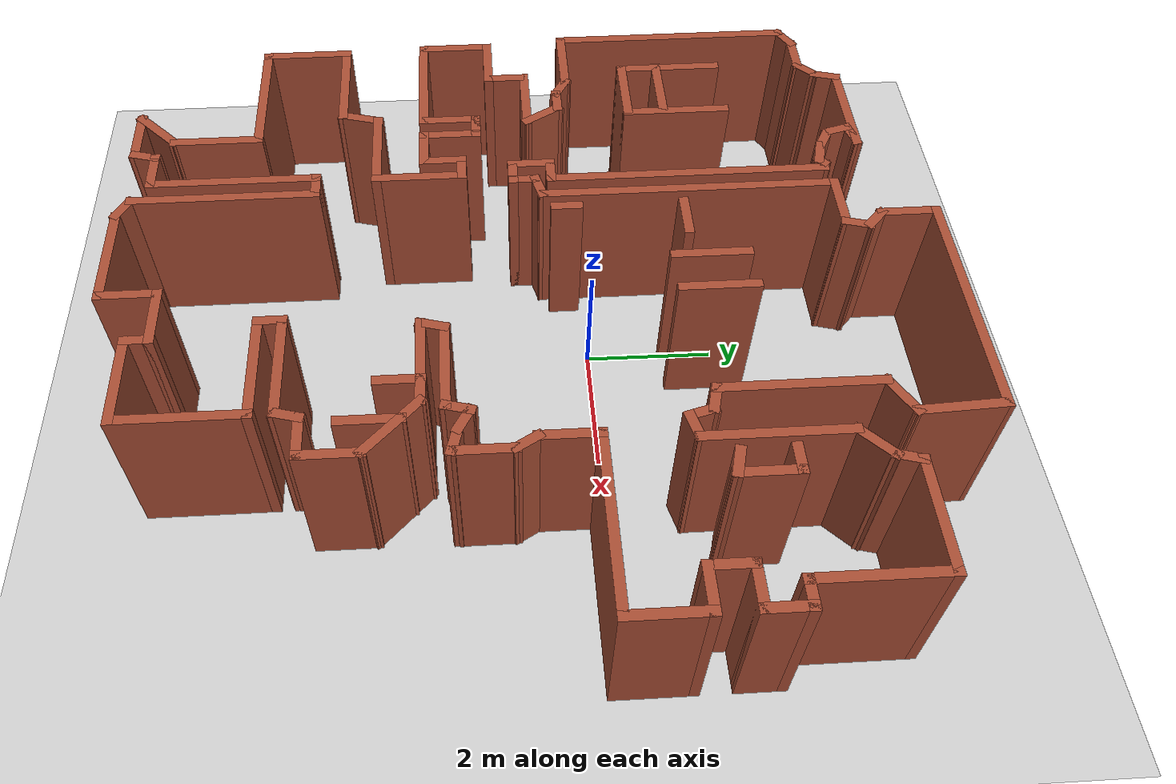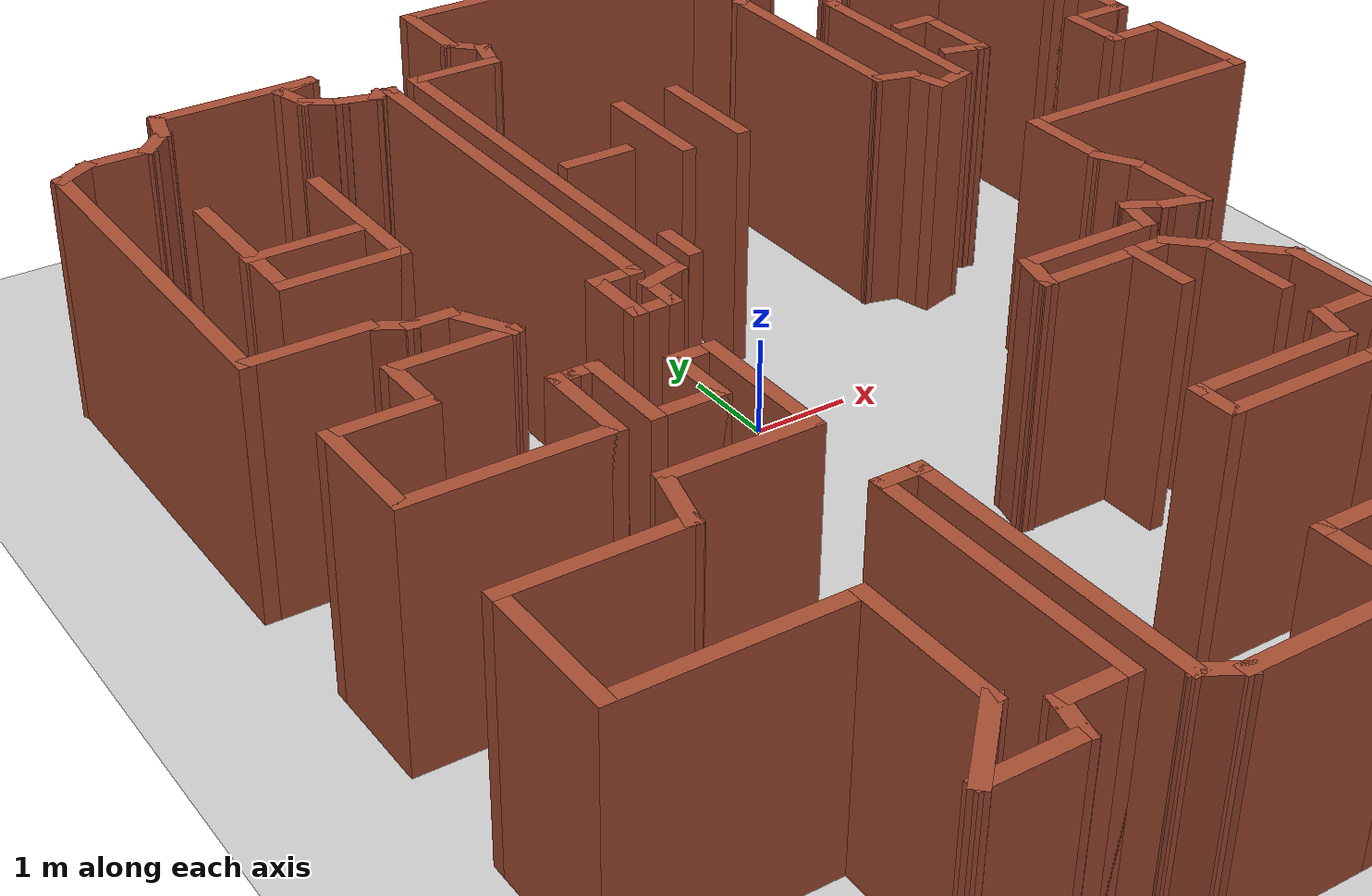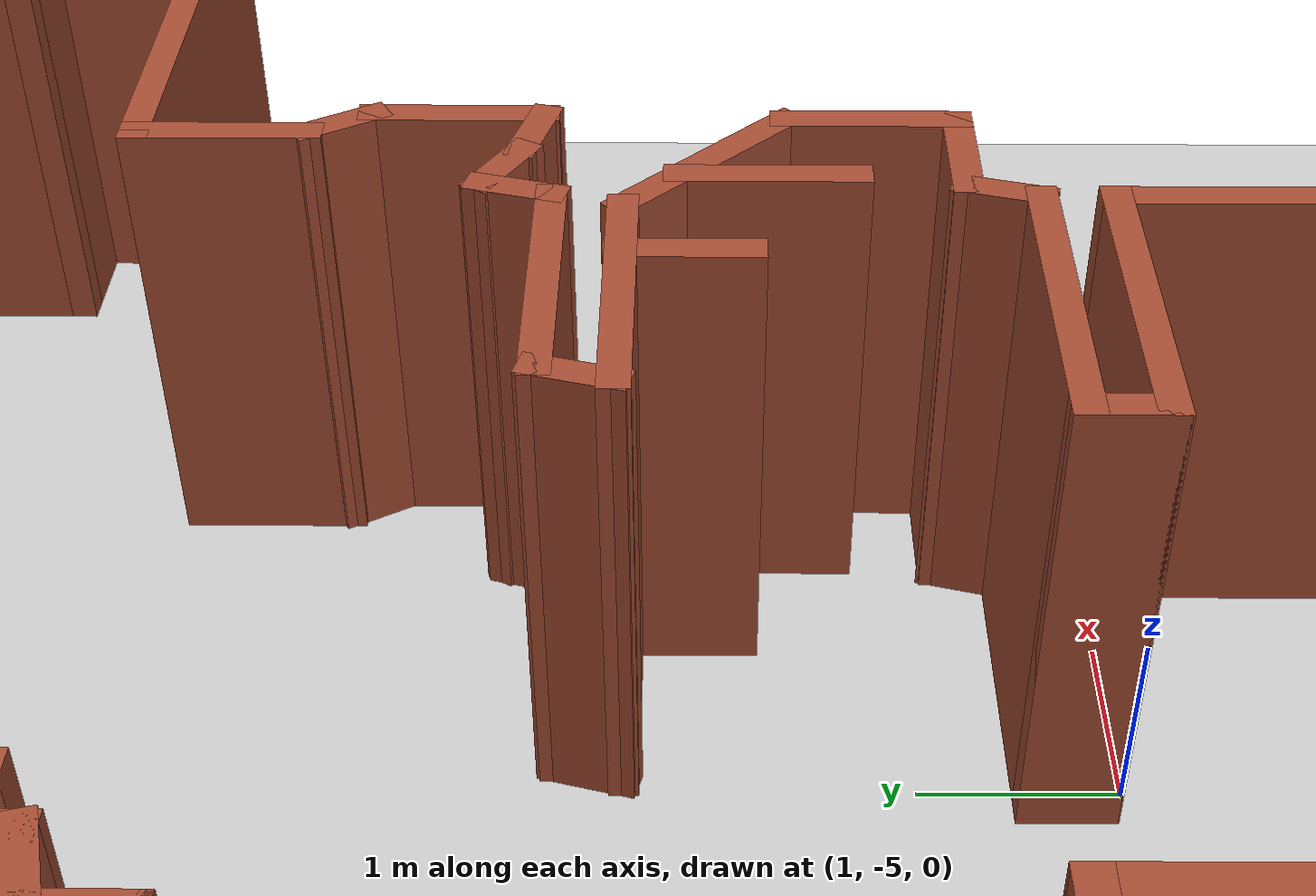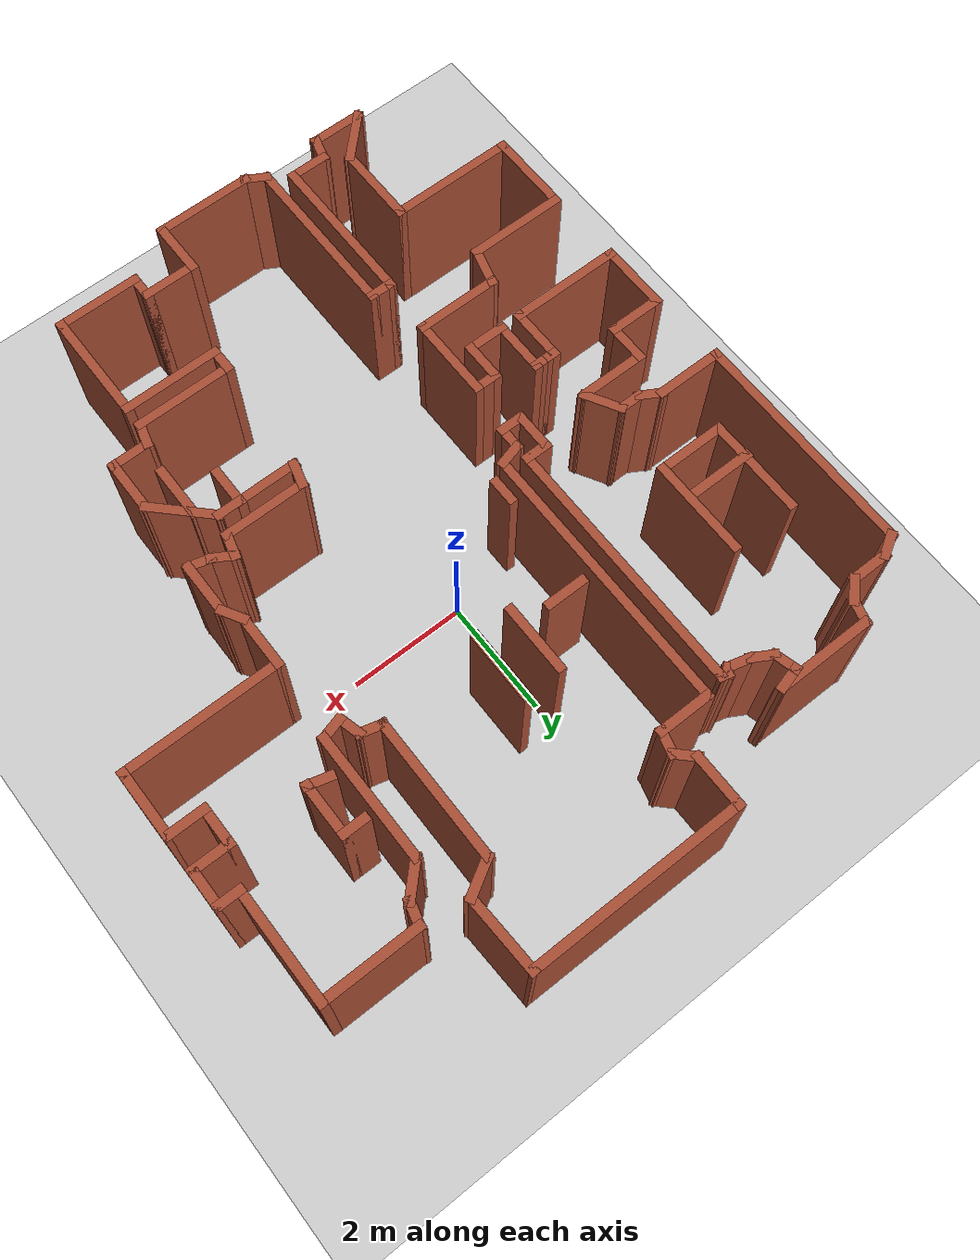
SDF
<sdf version="1.6">
 <world name="default">
  <light name="sun" type="directional">
   <pose>0 0 10 0 -0 0</pose>
   <diffuse>0.8 0.8 0.8 1</diffuse>
   <specular>0.2 0.2 0.2 1</specular>
   <attenuation>
    <range>1000</range>
    <constant>0.9</constant>
    <linear>0.01</linear>
    <quadratic>0.001</quadratic>
   </attenuation>
   <direction>-0.5 0.1 -0.9</direction>
  </light>
  <model name="ground_plane">
   <static>1</static>
   <link name="link">
    <collision name="collision">
     <geometry><plane><normal>0 0 1</normal><size>100 100</size></plane></geometry>
     <surface>
      <contact><collide_bitmask>65535</collide_bitmask></contact>
      <friction><ode><mu>100</mu><mu2>50</mu2></ode></friction>
     </surface>
    </collision>
    <visual name="visual">
     <cast_shadows>0</cast_shadows>
     <geometry><plane><normal>0 0 1</normal><size>100 100</size></plane></geometry>
     <material>
      <script><uri>file://media/materials/scripts/gazebo.material</uri><name>Gazebo/Grey</name></script>
     </material>
    </visual>
   </link>
  </model>
  <gravity>0 0 -9.8</gravity>
  <magnetic_field>6e-06 2.3e-05 -4.2e-05</magnetic_field>
  <atmosphere type="adiabatic"/>
  <physics name="default_physics" default="0" type="ode">
   <max_step_size>0.001</max_step_size>
   <real_time_factor>1</real_time_factor>
   <real_time_update_rate>1000</real_time_update_rate>
  </physics>
  <scene><ambient>0.4 0.4 0.4 1</ambient><background>0.7 0.7 0.7 1</background><shadows>1</shadows></scene>
  <audio><device>default</device></audio>
  <spherical_coordinates>
   <surface_model>EARTH_WGS84</surface_model>
   <latitude_deg>0</latitude_deg>
   <longitude_deg>0</longitude_deg>
   <elevation>0</elevation>
   <heading_deg>0</heading_deg>
  </spherical_coordinates>
  <model name="map_17">
   <pose>0.240525 -0.952018 0 0 -0 0</pose>
   <link name="Wall_0">
    <collision name="Wall_0_Collision">
     <geometry><box><size>3.75 0.15 2.5</size></box></geometry>
     <pose>0 0 1.25 0 -0 0</pose>
    </collision>
    <visual name="Wall_0_Visual">
     <pose>0 0 1.25 0 -0 0</pose>
     <geometry><box><size>3.75 0.15 2.5</size></box></geometry>
     <material>
      <script><uri>file://media/materials/scripts/gazebo.material</uri><name>Gazebo/Bricks</name></script>
      <ambient>1 1 1 1</ambient>
     </material>
     <meta><layer>0</layer></meta>
    </visual>
    <pose>0.846782 6.31181 0 0 -0 3.14159</pose>
   </link>
   <link name="Wall_1">
    <collision name="Wall_1_Collision">
     <geometry><box><size>1 0.15 2.5</size></box></geometry>
     <pose>0 0 1.25 0 -0 0</pose>
    </collision>
    <visual name="Wall_1_Visual">
     <pose>0 0 1.25 0 -0 0</pose>
     <geometry><box><size>1 0.15 2.5</size></box></geometry>
     <material>
      <script><uri>file://media/materials/scripts/gazebo.material</uri><name>Gazebo/Bricks</name></script>
      <ambient>1 1 1 1</ambient>
     </material>
     <meta><layer>0</layer></meta>
    </visual>
    <pose>-0.953218 5.88681 0 0 -0 -1.5708</pose>
   </link>
   <link name="Wall_10">
    <collision name="Wall_10_Collision">
     <geometry><box><size>0.5 0.15 2.5</size></box></geometry>
     <pose>0 0 1.25 0 -0 0</pose>
    </collision>
    <visual name="Wall_10_Visual">
     <pose>0 0 1.25 0 -0 0</pose>
     <geometry><box><size>0.5 0.15 2.5</size></box></geometry>
     <material>
      <script><uri>file://media/materials/scripts/gazebo.material</uri><name>Gazebo/Bricks</name></script>
      <ambient>1 1 1 1</ambient>
     </material>
     <meta><layer>0</layer></meta>
    </visual>
    <pose>-2.15939 0.435665 0 0 -0 0</pose>
   </link>
   <link name="Wall_100">
    <collision name="Wall_100_Collision">
     <geometry><box><size>0.5 0.15 2.5</size></box></geometry>
     <pose>0 0 1.25 0 -0 0</pose>
    </collision>
    <visual name="Wall_100_Visual">
     <pose>0 0 1.25 0 -0 0</pose>
     <geometry><box><size>0.5 0.15 2.5</size></box></geometry>
     <material>
      <script><uri>file://media/materials/scripts/gazebo.material</uri><name>Gazebo/Bricks</name></script>
      <ambient>1 1 1 1</ambient>
     </material>
     <meta><layer>0</layer></meta>
    </visual>
    <pose>2.56581 2.15806 0 0 -0 1.8326</pose>
   </link>
   <link name="Wall_101">
    <collision name="Wall_101_Collision">
     <geometry><box><size>0.5 0.15 2.5</size></box></geometry>
     <pose>0 0 1.25 0 -0 0</pose>
    </collision>
    <visual name="Wall_101_Visual">
     <pose>0 0 1.25 0 -0 0</pose>
     <geometry><box><size>0.5 0.15 2.5</size></box></geometry>
     <material>
      <script><uri>file://media/materials/scripts/gazebo.material</uri><name>Gazebo/Bricks</name></script>
      <ambient>1 1 1 1</ambient>
     </material>
     <meta><layer>0</layer></meta>
    </visual>
    <pose>2.35148 2.37239 0 0 -0 2.87979</pose>
   </link>
   <link name="Wall_102">
    <collision name="Wall_102_Collision">
     <geometry><box><size>2.5 0.15 2.5</size></box></geometry>
     <pose>0 0 1.25 0 -0 0</pose>
    </collision>
    <visual name="Wall_102_Visual">
     <pose>0 0 1.25 0 -0 0</pose>
     <geometry><box><size>2.5 0.15 2.5</size></box></geometry>
     <material>
      <script><uri>file://media/materials/scripts/gazebo.material</uri><name>Gazebo/Bricks</name></script>
      <ambient>1 1 1 1</ambient>
     </material>
     <meta><layer>0</layer></meta>
    </visual>
    <pose>2.18244 3.59268 0 0 -0 1.5708</pose>
   </link>
   <link name="Wall_103">
    <collision name="Wall_103_Collision">
     <geometry><box><size>0.75 0.15 2.5</size></box></geometry>
     <pose>0 0 1.25 0 -0 0</pose>
    </collision>
    <visual name="Wall_103_Visual">
     <pose>0 0 1.25 0 -0 0</pose>
     <geometry><box><size>0.75 0.15 2.5</size></box></geometry>
     <material>
      <script><uri>file://media/materials/scripts/gazebo.material</uri><name>Gazebo/Bricks</name></script>
      <ambient>1 1 1 1</ambient>
     </material>
     <meta><layer>0</layer></meta>
    </visual>
    <pose>2.44225 4.91768 0 0 -0 0.523599</pose>
   </link>
   <link name="Wall_104">
    <collision name="Wall_104_Collision">
     <geometry><box><size>1.39536 0.15 2.5</size></box></geometry>
     <pose>0 0 1.25 0 -0 0</pose>
    </collision>
    <visual name="Wall_104_Visual">
     <pose>0 0 1.25 0 -0 0</pose>
     <geometry><box><size>1.39536 0.15 2.5</size></box></geometry>
     <material>
      <script><uri>file://media/materials/scripts/gazebo.material</uri><name>Gazebo/Bricks</name></script>
      <ambient>1 1 1 1</ambient>
     </material>
     <meta><layer>0</layer></meta>
    </visual>
    <pose>2.67442 5.68975 0 0 -0 1.61519</pose>
   </link>
   <link name="Wall_106">
    <collision name="Wall_106_Collision">
     <geometry><box><size>1.75 0.15 2.5</size></box></geometry>
     <pose>0 0 1.25 0 -0 0</pose>
    </collision>
    <visual name="Wall_106_Visual">
     <pose>0 0 1.25 0 -0 0</pose>
     <geometry><box><size>1.75 0.15 2.5</size></box></geometry>
     <material>
      <script><uri>file://media/materials/scripts/gazebo.material</uri><name>Gazebo/Bricks</name></script>
      <ambient>1 1 1 1</ambient>
     </material>
     <meta><layer>0</layer></meta>
    </visual>
    <pose>-4.56187 2.61239 0 0 -0 -1.5708</pose>
   </link>
   <link name="Wall_107">
    <collision name="Wall_107_Collision">
     <geometry><box><size>1.25 0.15 2.5</size></box></geometry>
     <pose>0 0 1.25 0 -0 0</pose>
    </collision>
    <visual name="Wall_107_Visual">
     <pose>0 0 1.25 0 -0 0</pose>
     <geometry><box><size>1.25 0.15 2.5</size></box></geometry>
     <material>
      <script><uri>file://media/materials/scripts/gazebo.material</uri><name>Gazebo/Bricks</name></script>
      <ambient>1 1 1 1</ambient>
     </material>
     <meta><layer>0</layer></meta>
    </visual>
    <pose>-4.01187 1.81239 0 0 -0 0</pose>
   </link>
   <link name="Wall_108">
    <collision name="Wall_108_Collision">
     <geometry><box><size>1.75 0.15 2.5</size></box></geometry>
     <pose>0 0 1.25 0 -0 0</pose>
    </collision>
    <visual name="Wall_108_Visual">
     <pose>0 0 1.25 0 -0 0</pose>
     <geometry><box><size>1.75 0.15 2.5</size></box></geometry>
     <material>
      <script><uri>file://media/materials/scripts/gazebo.material</uri><name>Gazebo/Bricks</name></script>
      <ambient>1 1 1 1</ambient>
     </material>
     <meta><layer>0</layer></meta>
    </visual>
    <pose>-3.46187 2.61239 0 0 -0 1.5708</pose>
   </link>
   <link name="Wall_11">
    <collision name="Wall_11_Collision">
     <geometry><box><size>4.5 0.15 2.5</size></box></geometry>
     <pose>0 0 1.25 0 -0 0</pose>
    </collision>
    <visual name="Wall_11_Visual">
     <pose>0 0 1.25 0 -0 0</pose>
     <geometry><box><size>4.5 0.15 2.5</size></box></geometry>
     <material>
      <script><uri>file://media/materials/scripts/gazebo.material</uri><name>Gazebo/Bricks</name></script>
      <ambient>1 1 1 1</ambient>
     </material>
     <meta><layer>0</layer></meta>
    </visual>
    <pose>-1.98439 2.61066 0 0 -0 1.5708</pose>
   </link>
   <link name="Wall_110">
    <collision name="Wall_110_Collision">
     <geometry><box><size>1.25 0.15 2.5</size></box></geometry>
     <pose>0 0 1.25 0 -0 0</pose>
    </collision>
    <visual name="Wall_110_Visual">
     <pose>0 0 1.25 0 -0 0</pose>
     <geometry><box><size>1.25 0.15 2.5</size></box></geometry>
     <material>
      <script><uri>file://media/materials/scripts/gazebo.material</uri><name>Gazebo/Bricks</name></script>
      <ambient>1 1 1 1</ambient>
     </material>
     <meta><layer>0</layer></meta>
    </visual>
    <pose>-4.03847 2.40158 0 0 -0 0</pose>
   </link>
   <link name="Wall_112">
    <collision name="Wall_112_Collision">
     <geometry><box><size>1.25 0.15 2.5</size></box></geometry>
     <pose>0 0 1.25 0 -0 0</pose>
    </collision>
    <visual name="Wall_112_Visual">
     <pose>0 0 1.25 0 -0 0</pose>
     <geometry><box><size>1.25 0.15 2.5</size></box></geometry>
     <material>
      <script><uri>file://media/materials/scripts/gazebo.material</uri><name>Gazebo/Bricks</name></script>
      <ambient>1 1 1 1</ambient>
     </material>
     <meta><layer>0</layer></meta>
    </visual>
    <pose>-0.27924 2.72939 0 0 -0 -1.5708</pose>
   </link>
   <link name="Wall_114">
    <collision name="Wall_114_Collision">
     <geometry><box><size>1.25 0.15 2.5</size></box></geometry>
     <pose>0 0 1.25 0 -0 0</pose>
    </collision>
    <visual name="Wall_114_Visual">
     <pose>0 0 1.25 0 -0 0</pose>
     <geometry><box><size>1.25 0.15 2.5</size></box></geometry>
     <material>
      <script><uri>file://media/materials/scripts/gazebo.material</uri><name>Gazebo/Bricks</name></script>
      <ambient>1 1 1 1</ambient>
     </material>
     <meta><layer>0</layer></meta>
    </visual>
    <pose>0.359165 2.75599 0 0 -0 -1.5708</pose>
   </link>
   <link name="Wall_116">
    <collision name="Wall_116_Collision">
     <geometry><box><size>0.75 0.15 2.5</size></box></geometry>
     <pose>0 0 1.25 0 -0 0</pose>
    </collision>
    <visual name="Wall_116_Visual">
     <pose>0 0 1.25 0 -0 0</pose>
     <geometry><box><size>0.75 0.15 2.5</size></box></geometry>
     <material>
      <script><uri>file://media/materials/scripts/gazebo.material</uri><name>Gazebo/Bricks</name></script>
      <ambient>1 1 1 1</ambient>
     </material>
     <meta><layer>0</layer></meta>
    </visual>
    <pose>-1.06985 2.45478 0 0 -0 0</pose>
   </link>
   <link name="Wall_118">
    <collision name="Wall_118_Collision">
     <geometry><box><size>0.5 0.15 2.5</size></box></geometry>
     <pose>0 0 1.25 0 -0 0</pose>
    </collision>
    <visual name="Wall_118_Visual">
     <pose>0 0 1.25 0 -0 0</pose>
     <geometry><box><size>0.5 0.15 2.5</size></box></geometry>
     <material>
      <script><uri>file://media/materials/scripts/gazebo.material</uri><name>Gazebo/Bricks</name></script>
      <ambient>1 1 1 1</ambient>
     </material>
     <meta><layer>0</layer></meta>
    </visual>
    <pose>3.35379 3.33259 0 0 -0 0</pose>
   </link>
   <link name="Wall_119">
    <collision name="Wall_119_Collision">
     <geometry><box><size>1 0.15 2.5</size></box></geometry>
     <pose>0 0 1.25 0 -0 0</pose>
    </collision>
    <visual name="Wall_119_Visual">
     <pose>0 0 1.25 0 -0 0</pose>
     <geometry><box><size>1 0.15 2.5</size></box></geometry>
     <material>
      <script><uri>file://media/materials/scripts/gazebo.material</uri><name>Gazebo/Bricks</name></script>
      <ambient>1 1 1 1</ambient>
     </material>
     <meta><layer>0</layer></meta>
    </visual>
    <pose>3.52879 2.90759 0 0 -0 -1.5708</pose>
   </link>
   <link name="Wall_12">
    <collision name="Wall_12_Collision">
     <geometry><box><size>0.25 0.15 2.5</size></box></geometry>
     <pose>0 0 1.25 0 -0 0</pose>
    </collision>
    <visual name="Wall_12_Visual">
     <pose>0 0 1.25 0 -0 0</pose>
     <geometry><box><size>0.25 0.15 2.5</size></box></geometry>
     <material>
      <script><uri>file://media/materials/scripts/gazebo.material</uri><name>Gazebo/Bricks</name></script>
      <ambient>1 1 1 1</ambient>
     </material>
     <meta><layer>0</layer></meta>
    </visual>
    <pose>-2.03269 4.79861 0 0 -0 2.87979</pose>
   </link>
   <link name="Wall_120">
    <collision name="Wall_120_Collision">
     <geometry><box><size>0.5 0.15 2.5</size></box></geometry>
     <pose>0 0 1.25 0 -0 0</pose>
    </collision>
    <visual name="Wall_120_Visual">
     <pose>0 0 1.25 0 -0 0</pose>
     <geometry><box><size>0.5 0.15 2.5</size></box></geometry>
     <material>
      <script><uri>file://media/materials/scripts/gazebo.material</uri><name>Gazebo/Bricks</name></script>
      <ambient>1 1 1 1</ambient>
     </material>
     <meta><layer>0</layer></meta>
    </visual>
    <pose>3.35975 2.52788 0 0 -0 2.87979</pose>
   </link>
   <link name="Wall_122">
    <collision name="Wall_122_Collision">
     <geometry><box><size>0.75 0.15 2.5</size></box></geometry>
     <pose>0 0 1.25 0 -0 0</pose>
    </collision>
    <visual name="Wall_122_Visual">
     <pose>0 0 1.25 0 -0 0</pose>
     <geometry><box><size>0.75 0.15 2.5</size></box></geometry>
     <material>
      <script><uri>file://media/materials/scripts/gazebo.material</uri><name>Gazebo/Bricks</name></script>
      <ambient>1 1 1 1</ambient>
     </material>
     <meta><layer>0</layer></meta>
    </visual>
    <pose>1.79557 -1.91505 0 0 -0 -1.5708</pose>
   </link>
   <link name="Wall_124">
    <collision name="Wall_124_Collision">
     <geometry><box><size>1 0.15 2.5</size></box></geometry>
     <pose>0 0 1.25 0 -0 0</pose>
    </collision>
    <visual name="Wall_124_Visual">
     <pose>0 0 1.25 0 -0 0</pose>
     <geometry><box><size>1 0.15 2.5</size></box></geometry>
     <material>
      <script><uri>file://media/materials/scripts/gazebo.material</uri><name>Gazebo/Bricks</name></script>
      <ambient>1 1 1 1</ambient>
     </material>
     <meta><layer>0</layer></meta>
    </visual>
    <pose>2.43398 -2.30605 0 0 -0 -1.5708</pose>
   </link>
   <link name="Wall_126">
    <collision name="Wall_126_Collision">
     <geometry><box><size>0.5 0.15 2.5</size></box></geometry>
     <pose>0 0 1.25 0 -0 0</pose>
    </collision>
    <visual name="Wall_126_Visual">
     <pose>0 0 1.25 0 -0 0</pose>
     <geometry><box><size>0.5 0.15 2.5</size></box></geometry>
     <material>
      <script><uri>file://media/materials/scripts/gazebo.material</uri><name>Gazebo/Bricks</name></script>
      <ambient>1 1 1 1</ambient>
     </material>
     <meta><layer>0</layer></meta>
    </visual>
    <pose>-1.36985 0.634769 0 0 -0 1.5708</pose>
   </link>
   <link name="Wall_13">
    <collision name="Wall_13_Collision">
     <geometry><box><size>0.25 0.15 2.5</size></box></geometry>
     <pose>0 0 1.25 0 -0 0</pose>
    </collision>
    <visual name="Wall_13_Visual">
     <pose>0 0 1.25 0 -0 0</pose>
     <geometry><box><size>0.25 0.15 2.5</size></box></geometry>
     <material>
      <script><uri>file://media/materials/scripts/gazebo.material</uri><name>Gazebo/Bricks</name></script>
      <ambient>1 1 1 1</ambient>
     </material>
     <meta><layer>0</layer></meta>
    </visual>
    <pose>-2.11634 4.77619 0 0 -0 -2.35619</pose>
   </link>
   <link name="Wall_14">
    <collision name="Wall_14_Collision">
     <geometry><box><size>0.5 0.15 2.5</size></box></geometry>
     <pose>0 0 1.25 0 -0 0</pose>
    </collision>
    <visual name="Wall_14_Visual">
     <pose>0 0 1.25 0 -0 0</pose>
     <geometry><box><size>0.5 0.15 2.5</size></box></geometry>
     <material>
      <script><uri>file://media/materials/scripts/gazebo.material</uri><name>Gazebo/Bricks</name></script>
      <ambient>1 1 1 1</ambient>
     </material>
     <meta><layer>0</layer></meta>
    </visual>
    <pose>-2.32073 4.78613 0 0 -0 2.87979</pose>
   </link>
   <link name="Wall_15">
    <collision name="Wall_15_Collision">
     <geometry><box><size>0.5 0.15 2.5</size></box></geometry>
     <pose>0 0 1.25 0 -0 0</pose>
    </collision>
    <visual name="Wall_15_Visual">
     <pose>0 0 1.25 0 -0 0</pose>
     <geometry><box><size>0.5 0.15 2.5</size></box></geometry>
     <material>
      <script><uri>file://media/materials/scripts/gazebo.material</uri><name>Gazebo/Bricks</name></script>
      <ambient>1 1 1 1</ambient>
     </material>
     <meta><layer>0</layer></meta>
    </visual>
    <pose>-2.64132 4.91892 0 0 -0 2.61799</pose>
   </link>
   <link name="Wall_16">
    <collision name="Wall_16_Collision">
     <geometry><box><size>0.5 0.15 2.5</size></box></geometry>
     <pose>0 0 1.25 0 -0 0</pose>
    </collision>
    <visual name="Wall_16_Visual">
     <pose>0 0 1.25 0 -0 0</pose>
     <geometry><box><size>0.5 0.15 2.5</size></box></geometry>
     <material>
      <script><uri>file://media/materials/scripts/gazebo.material</uri><name>Gazebo/Bricks</name></script>
      <ambient>1 1 1 1</ambient>
     </material>
     <meta><layer>0</layer></meta>
    </visual>
    <pose>-2.83817 5.17546 0 0 -0 1.8326</pose>
   </link>
   <link name="Wall_17">
    <collision name="Wall_17_Collision">
     <geometry><box><size>0.5 0.15 2.5</size></box></geometry>
     <pose>0 0 1.25 0 -0 0</pose>
    </collision>
    <visual name="Wall_17_Visual">
     <pose>0 0 1.25 0 -0 0</pose>
     <geometry><box><size>0.5 0.15 2.5</size></box></geometry>
     <material>
      <script><uri>file://media/materials/scripts/gazebo.material</uri><name>Gazebo/Bricks</name></script>
      <ambient>1 1 1 1</ambient>
     </material>
     <meta><layer>0</layer></meta>
    </visual>
    <pose>-2.71443 5.38979 0 0 -0 0.261799</pose>
   </link>
   <link name="Wall_18">
    <collision name="Wall_18_Collision">
     <geometry><box><size>1.75 0.15 2.5</size></box></geometry>
     <pose>0 0 1.25 0 -0 0</pose>
    </collision>
    <visual name="Wall_18_Visual">
     <pose>0 0 1.25 0 -0 0</pose>
     <geometry><box><size>1.75 0.15 2.5</size></box></geometry>
     <material>
      <script><uri>file://media/materials/scripts/gazebo.material</uri><name>Gazebo/Bricks</name></script>
      <ambient>1 1 1 1</ambient>
     </material>
     <meta><layer>0</layer></meta>
    </visual>
    <pose>-3.34539 5.43508 0 0 -0 3.14159</pose>
   </link>
   <link name="Wall_19">
    <collision name="Wall_19_Collision">
     <geometry><box><size>0.5 0.15 2.5</size></box></geometry>
     <pose>0 0 1.25 0 -0 0</pose>
    </collision>
    <visual name="Wall_19_Visual">
     <pose>0 0 1.25 0 -0 0</pose>
     <geometry><box><size>0.5 0.15 2.5</size></box></geometry>
     <material>
      <script><uri>file://media/materials/scripts/gazebo.material</uri><name>Gazebo/Bricks</name></script>
      <ambient>1 1 1 1</ambient>
     </material>
     <meta><layer>0</layer></meta>
    </visual>
    <pose>-4.19068 5.26605 0 0 -0 -1.8326</pose>
   </link>
   <link name="Wall_2">
    <collision name="Wall_2_Collision">
     <geometry><box><size>0.5 0.15 2.5</size></box></geometry>
     <pose>0 0 1.25 0 -0 0</pose>
    </collision>
    <visual name="Wall_2_Visual">
     <pose>0 0 1.25 0 -0 0</pose>
     <geometry><box><size>0.5 0.15 2.5</size></box></geometry>
     <material>
      <script><uri>file://media/materials/scripts/gazebo.material</uri><name>Gazebo/Bricks</name></script>
      <ambient>1 1 1 1</ambient>
     </material>
     <meta><layer>0</layer></meta>
    </visual>
    <pose>-0.829474 5.33807 0 0 -0 -0.785398</pose>
   </link>
   <link name="Wall_20">
    <collision name="Wall_20_Collision">
     <geometry><box><size>0.5 0.15 2.5</size></box></geometry>
     <pose>0 0 1.25 0 -0 0</pose>
    </collision>
    <visual name="Wall_20_Visual">
     <pose>0 0 1.25 0 -0 0</pose>
     <geometry><box><size>0.5 0.15 2.5</size></box></geometry>
     <material>
      <script><uri>file://media/materials/scripts/gazebo.material</uri><name>Gazebo/Bricks</name></script>
      <ambient>1 1 1 1</ambient>
     </material>
     <meta><layer>0</layer></meta>
    </visual>
    <pose>-4.35972 4.97326 0 0 -0 -2.35619</pose>
   </link>
   <link name="Wall_21">
    <collision name="Wall_21_Collision">
     <geometry><box><size>0.75 0.15 2.5</size></box></geometry>
     <pose>0 0 1.25 0 -0 0</pose>
    </collision>
    <visual name="Wall_21_Visual">
     <pose>0 0 1.25 0 -0 0</pose>
     <geometry><box><size>0.75 0.15 2.5</size></box></geometry>
     <material>
      <script><uri>file://media/materials/scripts/gazebo.material</uri><name>Gazebo/Bricks</name></script>
      <ambient>1 1 1 1</ambient>
     </material>
     <meta><layer>0</layer></meta>
    </visual>
    <pose>-4.78346 4.84952 0 0 -0 3.14159</pose>
   </link>
   <link name="Wall_22">
    <collision name="Wall_22_Collision">
     <geometry><box><size>0.5 0.15 2.5</size></box></geometry>
     <pose>0 0 1.25 0 -0 0</pose>
    </collision>
    <visual name="Wall_22_Visual">
     <pose>0 0 1.25 0 -0 0</pose>
     <geometry><box><size>0.5 0.15 2.5</size></box></geometry>
     <material>
      <script><uri>file://media/materials/scripts/gazebo.material</uri><name>Gazebo/Bricks</name></script>
      <ambient>1 1 1 1</ambient>
     </material>
     <meta><layer>0</layer></meta>
    </visual>
    <pose>-5.23502 4.76202 0 0 -0 -2.61799</pose>
   </link>
   <link name="Wall_23">
    <collision name="Wall_23_Collision">
     <geometry><box><size>4 0.15 2.5</size></box></geometry>
     <pose>0 0 1.25 0 -0 0</pose>
    </collision>
    <visual name="Wall_23_Visual">
     <pose>0 0 1.25 0 -0 0</pose>
     <geometry><box><size>4 0.15 2.5</size></box></geometry>
     <material>
      <script><uri>file://media/materials/scripts/gazebo.material</uri><name>Gazebo/Bricks</name></script>
      <ambient>1 1 1 1</ambient>
     </material>
     <meta><layer>0</layer></meta>
    </visual>
    <pose>-5.38657 2.74952 0 0 -0 -1.5708</pose>
   </link>
   <link name="Wall_24">
    <collision name="Wall_24_Collision">
     <geometry><box><size>1.25 0.15 2.5</size></box></geometry>
     <pose>0 0 1.25 0 -0 0</pose>
    </collision>
    <visual name="Wall_24_Visual">
     <pose>0 0 1.25 0 -0 0</pose>
     <geometry><box><size>1.25 0.15 2.5</size></box></geometry>
     <material>
      <script><uri>file://media/materials/scripts/gazebo.material</uri><name>Gazebo/Bricks</name></script>
      <ambient>1 1 1 1</ambient>
     </material>
     <meta><layer>0</layer></meta>
    </visual>
    <pose>-4.83657 0.824522 0 0 -0 0</pose>
   </link>
   <link name="Wall_25">
    <collision name="Wall_25_Collision">
     <geometry><box><size>0.5 0.15 2.5</size></box></geometry>
     <pose>0 0 1.25 0 -0 0</pose>
    </collision>
    <visual name="Wall_25_Visual">
     <pose>0 0 1.25 0 -0 0</pose>
     <geometry><box><size>0.5 0.15 2.5</size></box></geometry>
     <material>
      <script><uri>file://media/materials/scripts/gazebo.material</uri><name>Gazebo/Bricks</name></script>
      <ambient>1 1 1 1</ambient>
     </material>
     <meta><layer>0</layer></meta>
    </visual>
    <pose>-4.13502 0.737022 0 0 -0 -0.523599</pose>
   </link>
   <link name="Wall_26">
    <collision name="Wall_26_Collision">
     <geometry><box><size>0.5 0.15 2.5</size></box></geometry>
     <pose>0 0 1.25 0 -0 0</pose>
    </collision>
    <visual name="Wall_26_Visual">
     <pose>0 0 1.25 0 -0 0</pose>
     <geometry><box><size>0.5 0.15 2.5</size></box></geometry>
     <material>
      <script><uri>file://media/materials/scripts/gazebo.material</uri><name>Gazebo/Bricks</name></script>
      <ambient>1 1 1 1</ambient>
     </material>
     <meta><layer>0</layer></meta>
    </visual>
    <pose>-3.80846 0.649522 0 0 -0 0</pose>
   </link>
   <link name="Wall_27">
    <collision name="Wall_27_Collision">
     <geometry><box><size>0.75 0.15 2.5</size></box></geometry>
     <pose>0 0 1.25 0 -0 0</pose>
    </collision>
    <visual name="Wall_27_Visual">
     <pose>0 0 1.25 0 -0 0</pose>
     <geometry><box><size>0.75 0.15 2.5</size></box></geometry>
     <material>
      <script><uri>file://media/materials/scripts/gazebo.material</uri><name>Gazebo/Bricks</name></script>
      <ambient>1 1 1 1</ambient>
     </material>
     <meta><layer>0</layer></meta>
    </visual>
    <pose>-3.48346 0.389714 0 0 -0 -1.0472</pose>
   </link>
   <link name="Wall_28">
    <collision name="Wall_28_Collision">
     <geometry><box><size>1.25 0.15 2.5</size></box></geometry>
     <pose>0 0 1.25 0 -0 0</pose>
    </collision>
    <visual name="Wall_28_Visual">
     <pose>0 0 1.25 0 -0 0</pose>
     <geometry><box><size>1.25 0.15 2.5</size></box></geometry>
     <material>
      <script><uri>file://media/materials/scripts/gazebo.material</uri><name>Gazebo/Bricks</name></script>
      <ambient>1 1 1 1</ambient>
     </material>
     <meta><layer>0</layer></meta>
    </visual>
    <pose>-3.88346 0.129907 0 0 -0 3.14159</pose>
   </link>
   <link name="Wall_29">
    <collision name="Wall_29_Collision">
     <geometry><box><size>0.75 0.15 2.5</size></box></geometry>
     <pose>0 0 1.25 0 -0 0</pose>
    </collision>
    <visual name="Wall_29_Visual">
     <pose>0 0 1.25 0 -0 0</pose>
     <geometry><box><size>0.75 0.15 2.5</size></box></geometry>
     <material>
      <script><uri>file://media/materials/scripts/gazebo.material</uri><name>Gazebo/Bricks</name></script>
      <ambient>1 1 1 1</ambient>
     </material>
     <meta><layer>0</layer></meta>
    </visual>
    <pose>-4.43346 -0.170094 0 0 -0 -1.5708</pose>
   </link>
   <link name="Wall_3">
    <collision name="Wall_3_Collision">
     <geometry><box><size>0.5 0.15 2.5</size></box></geometry>
     <pose>0 0 1.25 0 -0 0</pose>
    </collision>
    <visual name="Wall_3_Visual">
     <pose>0 0 1.25 0 -0 0</pose>
     <geometry><box><size>0.5 0.15 2.5</size></box></geometry>
     <material>
      <script><uri>file://media/materials/scripts/gazebo.material</uri><name>Gazebo/Bricks</name></script>
      <ambient>1 1 1 1</ambient>
     </material>
     <meta><layer>0</layer></meta>
    </visual>
    <pose>-0.751024 5.04529 0 0 -0 -1.8326</pose>
   </link>
   <link name="Wall_30">
    <collision name="Wall_30_Collision">
     <geometry><box><size>1 0.15 2.5</size></box></geometry>
     <pose>0 0 1.25 0 -0 0</pose>
    </collision>
    <visual name="Wall_30_Visual">
     <pose>0 0 1.25 0 -0 0</pose>
     <geometry><box><size>1 0.15 2.5</size></box></geometry>
     <material>
      <script><uri>file://media/materials/scripts/gazebo.material</uri><name>Gazebo/Bricks</name></script>
      <ambient>1 1 1 1</ambient>
     </material>
     <meta><layer>0</layer></meta>
    </visual>
    <pose>-4.85846 -0.470094 0 0 -0 3.14159</pose>
   </link>
   <link name="Wall_31">
    <collision name="Wall_31_Collision">
     <geometry><box><size>1.25 0.15 2.5</size></box></geometry>
     <pose>0 0 1.25 0 -0 0</pose>
    </collision>
    <visual name="Wall_31_Visual">
     <pose>0 0 1.25 0 -0 0</pose>
     <geometry><box><size>1.25 0.15 2.5</size></box></geometry>
     <material>
      <script><uri>file://media/materials/scripts/gazebo.material</uri><name>Gazebo/Bricks</name></script>
      <ambient>1 1 1 1</ambient>
     </material>
     <meta><layer>0</layer></meta>
    </visual>
    <pose>-5.28346 -1.02009 0 0 -0 -1.5708</pose>
   </link>
   <link name="Wall_32">
    <collision name="Wall_32_Collision">
     <geometry><box><size>2 0.15 2.5</size></box></geometry>
     <pose>0 0 1.25 0 -0 0</pose>
    </collision>
    <visual name="Wall_32_Visual">
     <pose>0 0 1.25 0 -0 0</pose>
     <geometry><box><size>2 0.15 2.5</size></box></geometry>
     <material>
      <script><uri>file://media/materials/scripts/gazebo.material</uri><name>Gazebo/Bricks</name></script>
      <ambient>1 1 1 1</ambient>
     </material>
     <meta><layer>0</layer></meta>
    </visual>
    <pose>-4.35846 -1.57009 0 0 -0 0</pose>
   </link>
   <link name="Wall_33">
    <collision name="Wall_33_Collision">
     <geometry><box><size>1 0.15 2.5</size></box></geometry>
     <pose>0 0 1.25 0 -0 0</pose>
    </collision>
    <visual name="Wall_33_Visual">
     <pose>0 0 1.25 0 -0 0</pose>
     <geometry><box><size>1 0.15 2.5</size></box></geometry>
     <material>
      <script><uri>file://media/materials/scripts/gazebo.material</uri><name>Gazebo/Bricks</name></script>
      <ambient>1 1 1 1</ambient>
     </material>
     <meta><layer>0</layer></meta>
    </visual>
    <pose>-3.43346 -1.14509 0 0 -0 1.5708</pose>
   </link>
   <link name="Wall_34">
    <collision name="Wall_34_Collision">
     <geometry><box><size>0.25 0.15 2.5</size></box></geometry>
     <pose>0 0 1.25 0 -0 0</pose>
    </collision>
    <visual name="Wall_34_Visual">
     <pose>0 0 1.25 0 -0 0</pose>
     <geometry><box><size>0.25 0.15 2.5</size></box></geometry>
     <material>
      <script><uri>file://media/materials/scripts/gazebo.material</uri><name>Gazebo/Bricks</name></script>
      <ambient>1 1 1 1</ambient>
     </material>
     <meta><layer>0</layer></meta>
    </visual>
    <pose>-3.38346 -0.720094 0 0 -0 0</pose>
   </link>
   <link name="Wall_36">
    <collision name="Wall_36_Collision">
     <geometry><box><size>0.5 0.15 2.5</size></box></geometry>
     <pose>0 0 1.25 0 -0 0</pose>
    </collision>
    <visual name="Wall_36_Visual">
     <pose>0 0 1.25 0 -0 0</pose>
     <geometry><box><size>0.5 0.15 2.5</size></box></geometry>
     <material>
      <script><uri>file://media/materials/scripts/gazebo.material</uri><name>Gazebo/Bricks</name></script>
      <ambient>1 1 1 1</ambient>
     </material>
     <meta><layer>0</layer></meta>
    </visual>
    <pose>-3.25846 -0.720094 0 0 -0 0</pose>
   </link>
   <link name="Wall_37">
    <collision name="Wall_37_Collision">
     <geometry><box><size>1 0.15 2.5</size></box></geometry>
     <pose>0 0 1.25 0 -0 0</pose>
    </collision>
    <visual name="Wall_37_Visual">
     <pose>0 0 1.25 0 -0 0</pose>
     <geometry><box><size>1 0.15 2.5</size></box></geometry>
     <material>
      <script><uri>file://media/materials/scripts/gazebo.material</uri><name>Gazebo/Bricks</name></script>
      <ambient>1 1 1 1</ambient>
     </material>
     <meta><layer>0</layer></meta>
    </visual>
    <pose>-3.08346 -1.14509 0 0 -0 -1.5708</pose>
   </link>
   <link name="Wall_38">
    <collision name="Wall_38_Collision">
     <geometry><box><size>0.75 0.15 2.5</size></box></geometry>
     <pose>0 0 1.25 0 -0 0</pose>
    </collision>
    <visual name="Wall_38_Visual">
     <pose>0 0 1.25 0 -0 0</pose>
     <geometry><box><size>0.75 0.15 2.5</size></box></geometry>
     <material>
      <script><uri>file://media/materials/scripts/gazebo.material</uri><name>Gazebo/Bricks</name></script>
      <ambient>1 1 1 1</ambient>
     </material>
     <meta><layer>0</layer></meta>
    </visual>
    <pose>-2.78346 -1.57009 0 0 -0 0</pose>
   </link>
   <link name="Wall_39">
    <collision name="Wall_39_Collision">
     <geometry><box><size>0.75 0.15 2.5</size></box></geometry>
     <pose>0 0 1.25 0 -0 0</pose>
    </collision>
    <visual name="Wall_39_Visual">
     <pose>0 0 1.25 0 -0 0</pose>
     <geometry><box><size>0.75 0.15 2.5</size></box></geometry>
     <material>
      <script><uri>file://media/materials/scripts/gazebo.material</uri><name>Gazebo/Bricks</name></script>
      <ambient>1 1 1 1</ambient>
     </material>
     <meta><layer>0</layer></meta>
    </visual>
    <pose>-2.48346 -1.27009 0 0 -0 1.5708</pose>
   </link>
   <link name="Wall_4">
    <collision name="Wall_4_Collision">
     <geometry><box><size>1 0.15 2.5</size></box></geometry>
     <pose>0 0 1.25 0 -0 0</pose>
    </collision>
    <visual name="Wall_4_Visual">
     <pose>0 0 1.25 0 -0 0</pose>
     <geometry><box><size>1 0.15 2.5</size></box></geometry>
     <material>
      <script><uri>file://media/materials/scripts/gazebo.material</uri><name>Gazebo/Bricks</name></script>
      <ambient>1 1 1 1</ambient>
     </material>
     <meta><layer>0</layer></meta>
    </visual>
    <pose>-1.22132 4.87625 0 0 -0 3.14159</pose>
   </link>
   <link name="Wall_40">
    <collision name="Wall_40_Collision">
     <geometry><box><size>0.5 0.15 2.5</size></box></geometry>
     <pose>0 0 1.25 0 -0 0</pose>
    </collision>
    <visual name="Wall_40_Visual">
     <pose>0 0 1.25 0 -0 0</pose>
     <geometry><box><size>0.5 0.15 2.5</size></box></geometry>
     <material>
      <script><uri>file://media/materials/scripts/gazebo.material</uri><name>Gazebo/Bricks</name></script>
      <ambient>1 1 1 1</ambient>
     </material>
     <meta><layer>0</layer></meta>
    </visual>
    <pose>-2.30846 -0.970094 0 0 -0 0</pose>
   </link>
   <link name="Wall_41">
    <collision name="Wall_41_Collision">
     <geometry><box><size>1.5 0.15 2.5</size></box></geometry>
     <pose>0 0 1.25 0 -0 0</pose>
    </collision>
    <visual name="Wall_41_Visual">
     <pose>0 0 1.25 0 -0 0</pose>
     <geometry><box><size>1.5 0.15 2.5</size></box></geometry>
     <material>
      <script><uri>file://media/materials/scripts/gazebo.material</uri><name>Gazebo/Bricks</name></script>
      <ambient>1 1 1 1</ambient>
     </material>
     <meta><layer>0</layer></meta>
    </visual>
    <pose>-2.13346 -1.64509 0 0 -0 -1.5708</pose>
   </link>
   <link name="Wall_42">
    <collision name="Wall_42_Collision">
     <geometry><box><size>1.5 0.15 2.5</size></box></geometry>
     <pose>0 0 1.25 0 -0 0</pose>
    </collision>
    <visual name="Wall_42_Visual">
     <pose>0 0 1.25 0 -0 0</pose>
     <geometry><box><size>1.5 0.15 2.5</size></box></geometry>
     <material>
      <script><uri>file://media/materials/scripts/gazebo.material</uri><name>Gazebo/Bricks</name></script>
      <ambient>1 1 1 1</ambient>
     </material>
     <meta><layer>0</layer></meta>
    </visual>
    <pose>-2.80846 -2.32009 0 0 -0 3.14159</pose>
   </link>
   <link name="Wall_43">
    <collision name="Wall_43_Collision">
     <geometry><box><size>0.75 0.15 2.5</size></box></geometry>
     <pose>0 0 1.25 0 -0 0</pose>
    </collision>
    <visual name="Wall_43_Visual">
     <pose>0 0 1.25 0 -0 0</pose>
     <geometry><box><size>0.75 0.15 2.5</size></box></geometry>
     <material>
      <script><uri>file://media/materials/scripts/gazebo.material</uri><name>Gazebo/Bricks</name></script>
      <ambient>1 1 1 1</ambient>
     </material>
     <meta><layer>0</layer></meta>
    </visual>
    <pose>-3.56111 -2.60987 0 0 -0 -1.8326</pose>
   </link>
   <link name="Wall_44">
    <collision name="Wall_44_Collision">
     <geometry><box><size>1.75 0.15 2.5</size></box></geometry>
     <pose>0 0 1.25 0 -0 0</pose>
    </collision>
    <visual name="Wall_44_Visual">
     <pose>0 0 1.25 0 -0 0</pose>
     <geometry><box><size>1.75 0.15 2.5</size></box></geometry>
     <material>
      <script><uri>file://media/materials/scripts/gazebo.material</uri><name>Gazebo/Bricks</name></script>
      <ambient>1 1 1 1</ambient>
     </material>
     <meta><layer>0</layer></meta>
    </visual>
    <pose>-4.43876 -2.89965 0 0 -0 3.14159</pose>
   </link>
   <link name="Wall_45">
    <collision name="Wall_45_Collision">
     <geometry><box><size>1.5 0.15 2.5</size></box></geometry>
     <pose>0 0 1.25 0 -0 0</pose>
    </collision>
    <visual name="Wall_45_Visual">
     <pose>0 0 1.25 0 -0 0</pose>
     <geometry><box><size>1.5 0.15 2.5</size></box></geometry>
     <material>
      <script><uri>file://media/materials/scripts/gazebo.material</uri><name>Gazebo/Bricks</name></script>
      <ambient>1 1 1 1</ambient>
     </material>
     <meta><layer>0</layer></meta>
    </visual>
    <pose>-5.23876 -3.57465 0 0 -0 -1.5708</pose>
   </link>
   <link name="Wall_46">
    <collision name="Wall_46_Collision">
     <geometry><box><size>2.25 0.15 2.5</size></box></geometry>
     <pose>0 0 1.25 0 -0 0</pose>
    </collision>
    <visual name="Wall_46_Visual">
     <pose>0 0 1.25 0 -0 0</pose>
     <geometry><box><size>2.25 0.15 2.5</size></box></geometry>
     <material>
      <script><uri>file://media/materials/scripts/gazebo.material</uri><name>Gazebo/Bricks</name></script>
      <ambient>1 1 1 1</ambient>
     </material>
     <meta><layer>0</layer></meta>
    </visual>
    <pose>-4.18876 -4.24965 0 0 -0 0</pose>
   </link>
   <link name="Wall_47">
    <collision name="Wall_47_Collision">
     <geometry><box><size>1.5 0.15 2.5</size></box></geometry>
     <pose>0 0 1.25 0 -0 0</pose>
    </collision>
    <visual name="Wall_47_Visual">
     <pose>0 0 1.25 0 -0 0</pose>
     <geometry><box><size>1.5 0.15 2.5</size></box></geometry>
     <material>
      <script><uri>file://media/materials/scripts/gazebo.material</uri><name>Gazebo/Bricks</name></script>
      <ambient>1 1 1 1</ambient>
     </material>
     <meta><layer>0</layer></meta>
    </visual>
    <pose>-3.13876 -4.92465 0 0 -0 -1.5708</pose>
   </link>
   <link name="Wall_5">
    <collision name="Wall_5_Collision">
     <geometry><box><size>4.75 0.15 2.5</size></box></geometry>
     <pose>0 0 1.25 0 -0 0</pose>
    </collision>
    <visual name="Wall_5_Visual">
     <pose>0 0 1.25 0 -0 0</pose>
     <geometry><box><size>4.75 0.15 2.5</size></box></geometry>
     <material>
      <script><uri>file://media/materials/scripts/gazebo.material</uri><name>Gazebo/Bricks</name></script>
      <ambient>1 1 1 1</ambient>
     </material>
     <meta><layer>0</layer></meta>
    </visual>
    <pose>-1.64632 2.57625 0 0 -0 -1.5708</pose>
   </link>
   <link name="Wall_50">
    <collision name="Wall_50_Collision">
     <geometry><box><size>1 0.15 2.5</size></box></geometry>
     <pose>0 0 1.25 0 -0 0</pose>
    </collision>
    <visual name="Wall_50_Visual">
     <pose>0 0 1.25 0 -0 0</pose>
     <geometry><box><size>1 0.15 2.5</size></box></geometry>
     <material>
      <script><uri>file://media/materials/scripts/gazebo.material</uri><name>Gazebo/Bricks</name></script>
      <ambient>1 1 1 1</ambient>
     </material>
     <meta><layer>0</layer></meta>
    </visual>
    <pose>-3.43928 -5.90017 0 0 -0 -2.35619</pose>
   </link>
   <link name="Wall_51">
    <collision name="Wall_51_Collision">
     <geometry><box><size>1 0.15 2.5</size></box></geometry>
     <pose>0 0 1.25 0 -0 0</pose>
    </collision>
    <visual name="Wall_51_Visual">
     <pose>0 0 1.25 0 -0 0</pose>
     <geometry><box><size>1 0.15 2.5</size></box></geometry>
     <material>
      <script><uri>file://media/materials/scripts/gazebo.material</uri><name>Gazebo/Bricks</name></script>
      <ambient>1 1 1 1</ambient>
     </material>
     <meta><layer>0</layer></meta>
    </visual>
    <pose>-3.3148 -6.20069 0 0 -0 0</pose>
   </link>
   <link name="Wall_52">
    <collision name="Wall_52_Collision">
     <geometry><box><size>0.5 0.15 2.5</size></box></geometry>
     <pose>0 0 1.25 0 -0 0</pose>
    </collision>
    <visual name="Wall_52_Visual">
     <pose>0 0 1.25 0 -0 0</pose>
     <geometry><box><size>0.5 0.15 2.5</size></box></geometry>
     <material>
      <script><uri>file://media/materials/scripts/gazebo.material</uri><name>Gazebo/Bricks</name></script>
      <ambient>1 1 1 1</ambient>
     </material>
     <meta><layer>0</layer></meta>
    </visual>
    <pose>-2.8445 -6.03165 0 0 -0 1.309</pose>
   </link>
   <link name="Wall_53">
    <collision name="Wall_53_Collision">
     <geometry><box><size>0.75 0.15 2.5</size></box></geometry>
     <pose>0 0 1.25 0 -0 0</pose>
    </collision>
    <visual name="Wall_53_Visual">
     <pose>0 0 1.25 0 -0 0</pose>
     <geometry><box><size>0.75 0.15 2.5</size></box></geometry>
     <material>
      <script><uri>file://media/materials/scripts/gazebo.material</uri><name>Gazebo/Bricks</name></script>
      <ambient>1 1 1 1</ambient>
     </material>
     <meta><layer>0</layer></meta>
    </visual>
    <pose>-2.49921 -5.86262 0 0 -0 0</pose>
   </link>
   <link name="Wall_54">
    <collision name="Wall_54_Collision">
     <geometry><box><size>2.75 0.15 2.5</size></box></geometry>
     <pose>0 0 1.25 0 -0 0</pose>
    </collision>
    <visual name="Wall_54_Visual">
     <pose>0 0 1.25 0 -0 0</pose>
     <geometry><box><size>2.75 0.15 2.5</size></box></geometry>
     <material>
      <script><uri>file://media/materials/scripts/gazebo.material</uri><name>Gazebo/Bricks</name></script>
      <ambient>1 1 1 1</ambient>
     </material>
     <meta><layer>0</layer></meta>
    </visual>
    <pose>-2.19921 -4.56262 0 0 -0 1.5708</pose>
   </link>
   <link name="Wall_55">
    <collision name="Wall_55_Collision">
     <geometry><box><size>0.5 0.15 2.5</size></box></geometry>
     <pose>0 0 1.25 0 -0 0</pose>
    </collision>
    <visual name="Wall_55_Visual">
     <pose>0 0 1.25 0 -0 0</pose>
     <geometry><box><size>0.5 0.15 2.5</size></box></geometry>
     <material>
      <script><uri>file://media/materials/scripts/gazebo.material</uri><name>Gazebo/Bricks</name></script>
      <ambient>1 1 1 1</ambient>
     </material>
     <meta><layer>0</layer></meta>
    </visual>
    <pose>-2.02421 -3.26262 0 0 -0 0</pose>
   </link>
   <link name="Wall_56">
    <collision name="Wall_56_Collision">
     <geometry><box><size>3 0.15 2.5</size></box></geometry>
     <pose>0 0 1.25 0 -0 0</pose>
    </collision>
    <visual name="Wall_56_Visual">
     <pose>0 0 1.25 0 -0 0</pose>
     <geometry><box><size>3 0.15 2.5</size></box></geometry>
     <material>
      <script><uri>file://media/materials/scripts/gazebo.material</uri><name>Gazebo/Bricks</name></script>
      <ambient>1 1 1 1</ambient>
     </material>
     <meta><layer>0</layer></meta>
    </visual>
    <pose>-1.84921 -4.68762 0 0 -0 -1.5708</pose>
   </link>
   <link name="Wall_57">
    <collision name="Wall_57_Collision">
     <geometry><box><size>0.5 0.15 2.5</size></box></geometry>
     <pose>0 0 1.25 0 -0 0</pose>
    </collision>
    <visual name="Wall_57_Visual">
     <pose>0 0 1.25 0 -0 0</pose>
     <geometry><box><size>0.5 0.15 2.5</size></box></geometry>
     <material>
      <script><uri>file://media/materials/scripts/gazebo.material</uri><name>Gazebo/Bricks</name></script>
      <ambient>1 1 1 1</ambient>
     </material>
     <meta><layer>0</layer></meta>
    </visual>
    <pose>-1.69765 -6.20012 0 0 -0 -0.523599</pose>
   </link>
   <link name="Wall_58">
    <collision name="Wall_58_Collision">
     <geometry><box><size>1.75 0.15 2.5</size></box></geometry>
     <pose>0 0 1.25 0 -0 0</pose>
    </collision>
    <visual name="Wall_58_Visual">
     <pose>0 0 1.25 0 -0 0</pose>
     <geometry><box><size>1.75 0.15 2.5</size></box></geometry>
     <material>
      <script><uri>file://media/materials/scripts/gazebo.material</uri><name>Gazebo/Bricks</name></script>
      <ambient>1 1 1 1</ambient>
     </material>
     <meta><layer>0</layer></meta>
    </visual>
    <pose>-0.746101 -6.28761 0 0 -0 0</pose>
   </link>
   <link name="Wall_6">
    <collision name="Wall_6_Collision">
     <geometry><box><size>0.5 0.15 2.5</size></box></geometry>
     <pose>0 0 1.25 0 -0 0</pose>
    </collision>
    <visual name="Wall_6_Visual">
     <pose>0 0 1.25 0 -0 0</pose>
     <geometry><box><size>0.5 0.15 2.5</size></box></geometry>
     <material>
      <script><uri>file://media/materials/scripts/gazebo.material</uri><name>Gazebo/Bricks</name></script>
      <ambient>1 1 1 1</ambient>
     </material>
     <meta><layer>0</layer></meta>
    </visual>
    <pose>-1.81535 0.230958 0 0 -0 -2.87979</pose>
   </link>
   <link name="Wall_62">
    <collision name="Wall_62_Collision">
     <geometry><box><size>1 0.15 2.5</size></box></geometry>
     <pose>0 0 1.25 0 -0 0</pose>
    </collision>
    <visual name="Wall_62_Visual">
     <pose>0 0 1.25 0 -0 0</pose>
     <geometry><box><size>1 0.15 2.5</size></box></geometry>
     <material>
      <script><uri>file://media/materials/scripts/gazebo.material</uri><name>Gazebo/Bricks</name></script>
      <ambient>1 1 1 1</ambient>
     </material>
     <meta><layer>0</layer></meta>
    </visual>
    <pose>0.053899 -5.86262 0 0 -0 1.5708</pose>
   </link>
   <link name="Wall_63">
    <collision name="Wall_63_Collision">
     <geometry><box><size>1 0.15 2.5</size></box></geometry>
     <pose>0 0 1.25 0 -0 0</pose>
    </collision>
    <visual name="Wall_63_Visual">
     <pose>0 0 1.25 0 -0 0</pose>
     <geometry><box><size>1 0.15 2.5</size></box></geometry>
     <material>
      <script><uri>file://media/materials/scripts/gazebo.material</uri><name>Gazebo/Bricks</name></script>
      <ambient>1 1 1 1</ambient>
     </material>
     <meta><layer>0</layer></meta>
    </visual>
    <pose>0.478899 -5.43762 0 0 -0 0</pose>
   </link>
   <link name="Wall_64">
    <collision name="Wall_64_Collision">
     <geometry><box><size>0.5 0.15 2.5</size></box></geometry>
     <pose>0 0 1.25 0 -0 0</pose>
    </collision>
    <visual name="Wall_64_Visual">
     <pose>0 0 1.25 0 -0 0</pose>
     <geometry><box><size>0.5 0.15 2.5</size></box></geometry>
     <material>
      <script><uri>file://media/materials/scripts/gazebo.material</uri><name>Gazebo/Bricks</name></script>
      <ambient>1 1 1 1</ambient>
     </material>
     <meta><layer>0</layer></meta>
    </visual>
    <pose>0.903899 -5.61262 0 0 -0 -1.5708</pose>
   </link>
   <link name="Wall_65">
    <collision name="Wall_65_Collision">
     <geometry><box><size>1.5 0.15 2.5</size></box></geometry>
     <pose>0 0 1.25 0 -0 0</pose>
    </collision>
    <visual name="Wall_65_Visual">
     <pose>0 0 1.25 0 -0 0</pose>
     <geometry><box><size>1.5 0.15 2.5</size></box></geometry>
     <material>
      <script><uri>file://media/materials/scripts/gazebo.material</uri><name>Gazebo/Bricks</name></script>
      <ambient>1 1 1 1</ambient>
     </material>
     <meta><layer>0</layer></meta>
    </visual>
    <pose>1.5789 -5.78761 0 0 -0 0</pose>
   </link>
   <link name="Wall_66">
    <collision name="Wall_66_Collision">
     <geometry><box><size>2 0.15 2.5</size></box></geometry>
     <pose>0 0 1.25 0 -0 0</pose>
    </collision>
    <visual name="Wall_66_Visual">
     <pose>0 0 1.25 0 -0 0</pose>
     <geometry><box><size>2 0.15 2.5</size></box></geometry>
     <material>
      <script><uri>file://media/materials/scripts/gazebo.material</uri><name>Gazebo/Bricks</name></script>
      <ambient>1 1 1 1</ambient>
     </material>
     <meta><layer>0</layer></meta>
    </visual>
    <pose>2.2539 -4.86262 0 0 -0 1.5708</pose>
   </link>
   <link name="Wall_67">
    <collision name="Wall_67_Collision">
     <geometry><box><size>1.75 0.15 2.5</size></box></geometry>
     <pose>0 0 1.25 0 -0 0</pose>
    </collision>
    <visual name="Wall_67_Visual">
     <pose>0 0 1.25 0 -0 0</pose>
     <geometry><box><size>1.75 0.15 2.5</size></box></geometry>
     <material>
      <script><uri>file://media/materials/scripts/gazebo.material</uri><name>Gazebo/Bricks</name></script>
      <ambient>1 1 1 1</ambient>
     </material>
     <meta><layer>0</layer></meta>
    </visual>
    <pose>1.4539 -3.93762 0 0 -0 3.14159</pose>
   </link>
   <link name="Wall_68">
    <collision name="Wall_68_Collision">
     <geometry><box><size>0.5 0.15 2.5</size></box></geometry>
     <pose>0 0 1.25 0 -0 0</pose>
    </collision>
    <visual name="Wall_68_Visual">
     <pose>0 0 1.25 0 -0 0</pose>
     <geometry><box><size>0.5 0.15 2.5</size></box></geometry>
     <material>
      <script><uri>file://media/materials/scripts/gazebo.material</uri><name>Gazebo/Bricks</name></script>
      <ambient>1 1 1 1</ambient>
     </material>
     <meta><layer>0</layer></meta>
    </visual>
    <pose>0.653899 -3.76262 0 0 -0 1.5708</pose>
   </link>
   <link name="Wall_69">
    <collision name="Wall_69_Collision">
     <geometry><box><size>1.75 0.15 2.5</size></box></geometry>
     <pose>0 0 1.25 0 -0 0</pose>
    </collision>
    <visual name="Wall_69_Visual">
     <pose>0 0 1.25 0 -0 0</pose>
     <geometry><box><size>1.75 0.15 2.5</size></box></geometry>
     <material>
      <script><uri>file://media/materials/scripts/gazebo.material</uri><name>Gazebo/Bricks</name></script>
      <ambient>1 1 1 1</ambient>
     </material>
     <meta><layer>0</layer></meta>
    </visual>
    <pose>1.4539 -3.58762 0 0 -0 0</pose>
   </link>
   <link name="Wall_7">
    <collision name="Wall_7_Collision">
     <geometry><box><size>0.5 0.15 2.5</size></box></geometry>
     <pose>0 0 1.25 0 -0 0</pose>
    </collision>
    <visual name="Wall_7_Visual">
     <pose>0 0 1.25 0 -0 0</pose>
     <geometry><box><size>0.5 0.15 2.5</size></box></geometry>
     <material>
      <script><uri>file://media/materials/scripts/gazebo.material</uri><name>Gazebo/Bricks</name></script>
      <ambient>1 1 1 1</ambient>
     </material>
     <meta><layer>0</layer></meta>
    </visual>
    <pose>-1.98439 0.010664 0 0 -0 -1.5708</pose>
   </link>
   <link name="Wall_70">
    <collision name="Wall_70_Collision">
     <geometry><box><size>0.5 0.15 2.5</size></box></geometry>
     <pose>0 0 1.25 0 -0 0</pose>
    </collision>
    <visual name="Wall_70_Visual">
     <pose>0 0 1.25 0 -0 0</pose>
     <geometry><box><size>0.5 0.15 2.5</size></box></geometry>
     <material>
      <script><uri>file://media/materials/scripts/gazebo.material</uri><name>Gazebo/Bricks</name></script>
      <ambient>1 1 1 1</ambient>
     </material>
     <meta><layer>0</layer></meta>
    </visual>
    <pose>2.29919 -3.41858 0 0 -0 1.309</pose>
   </link>
   <link name="Wall_71">
    <collision name="Wall_71_Collision">
     <geometry><box><size>0.75 0.15 2.5</size></box></geometry>
     <pose>0 0 1.25 0 -0 0</pose>
    </collision>
    <visual name="Wall_71_Visual">
     <pose>0 0 1.25 0 -0 0</pose>
     <geometry><box><size>0.75 0.15 2.5</size></box></geometry>
     <material>
      <script><uri>file://media/materials/scripts/gazebo.material</uri><name>Gazebo/Bricks</name></script>
      <ambient>1 1 1 1</ambient>
     </material>
     <meta><layer>0</layer></meta>
    </visual>
    <pose>2.64449 -3.24954 0 0 -0 0</pose>
   </link>
   <link name="Wall_72">
    <collision name="Wall_72_Collision">
     <geometry><box><size>1 0.15 2.5</size></box></geometry>
     <pose>0 0 1.25 0 -0 0</pose>
    </collision>
    <visual name="Wall_72_Visual">
     <pose>0 0 1.25 0 -0 0</pose>
     <geometry><box><size>1 0.15 2.5</size></box></geometry>
     <material>
      <script><uri>file://media/materials/scripts/gazebo.material</uri><name>Gazebo/Bricks</name></script>
      <ambient>1 1 1 1</ambient>
     </material>
     <meta><layer>0</layer></meta>
    </visual>
    <pose>2.94449 -2.82454 0 0 -0 1.5708</pose>
   </link>
   <link name="Wall_73">
    <collision name="Wall_73_Collision">
     <geometry><box><size>1.25 0.15 2.5</size></box></geometry>
     <pose>0 0 1.25 0 -0 0</pose>
    </collision>
    <visual name="Wall_73_Visual">
     <pose>0 0 1.25 0 -0 0</pose>
     <geometry><box><size>1.25 0.15 2.5</size></box></geometry>
     <material>
      <script><uri>file://media/materials/scripts/gazebo.material</uri><name>Gazebo/Bricks</name></script>
      <ambient>1 1 1 1</ambient>
     </material>
     <meta><layer>0</layer></meta>
    </visual>
    <pose>2.55558 -2.01063 0 0 -0 2.35619</pose>
   </link>
   <link name="Wall_74">
    <collision name="Wall_74_Collision">
     <geometry><box><size>1.5 0.15 2.5</size></box></geometry>
     <pose>0 0 1.25 0 -0 0</pose>
    </collision>
    <visual name="Wall_74_Visual">
     <pose>0 0 1.25 0 -0 0</pose>
     <geometry><box><size>1.5 0.15 2.5</size></box></geometry>
     <material>
      <script><uri>file://media/materials/scripts/gazebo.material</uri><name>Gazebo/Bricks</name></script>
      <ambient>1 1 1 1</ambient>
     </material>
     <meta><layer>0</layer></meta>
    </visual>
    <pose>1.49167 -1.62172 0 0 -0 3.14159</pose>
   </link>
   <link name="Wall_75">
    <collision name="Wall_75_Collision">
     <geometry><box><size>0.5 0.15 2.5</size></box></geometry>
     <pose>0 0 1.25 0 -0 0</pose>
    </collision>
    <visual name="Wall_75_Visual">
     <pose>0 0 1.25 0 -0 0</pose>
     <geometry><box><size>0.5 0.15 2.5</size></box></geometry>
     <material>
      <script><uri>file://media/materials/scripts/gazebo.material</uri><name>Gazebo/Bricks</name></script>
      <ambient>1 1 1 1</ambient>
     </material>
     <meta><layer>0</layer></meta>
    </visual>
    <pose>0.861962 -1.45269 0 0 -0 1.309</pose>
   </link>
   <link name="Wall_76">
    <collision name="Wall_76_Collision">
     <geometry><box><size>1.5 0.15 2.5</size></box></geometry>
     <pose>0 0 1.25 0 -0 0</pose>
    </collision>
    <visual name="Wall_76_Visual">
     <pose>0 0 1.25 0 -0 0</pose>
     <geometry><box><size>1.5 0.15 2.5</size></box></geometry>
     <material>
      <script><uri>file://media/materials/scripts/gazebo.material</uri><name>Gazebo/Bricks</name></script>
      <ambient>1 1 1 1</ambient>
     </material>
     <meta><layer>0</layer></meta>
    </visual>
    <pose>1.58225 -1.28365 0 0 -0 0</pose>
   </link>
   <link name="Wall_77">
    <collision name="Wall_77_Collision">
     <geometry><box><size>0.5 0.15 2.5</size></box></geometry>
     <pose>0 0 1.25 0 -0 0</pose>
    </collision>
    <visual name="Wall_77_Visual">
     <pose>0 0 1.25 0 -0 0</pose>
     <geometry><box><size>0.5 0.15 2.5</size></box></geometry>
     <material>
      <script><uri>file://media/materials/scripts/gazebo.material</uri><name>Gazebo/Bricks</name></script>
      <ambient>1 1 1 1</ambient>
     </material>
     <meta><layer>0</layer></meta>
    </visual>
    <pose>2.30255 -1.11461 0 0 -0 1.309</pose>
   </link>
   <link name="Wall_78">
    <collision name="Wall_78_Collision">
     <geometry><box><size>0.5 0.15 2.5</size></box></geometry>
     <pose>0 0 1.25 0 -0 0</pose>
    </collision>
    <visual name="Wall_78_Visual">
     <pose>0 0 1.25 0 -0 0</pose>
     <geometry><box><size>0.5 0.15 2.5</size></box></geometry>
     <material>
      <script><uri>file://media/materials/scripts/gazebo.material</uri><name>Gazebo/Bricks</name></script>
      <ambient>1 1 1 1</ambient>
     </material>
     <meta><layer>0</layer></meta>
    </visual>
    <pose>2.4994 -1.03308 0 0 -0 -0.523599</pose>
   </link>
   <link name="Wall_79">
    <collision name="Wall_79_Collision">
     <geometry><box><size>0.5 0.15 2.5</size></box></geometry>
     <pose>0 0 1.25 0 -0 0</pose>
    </collision>
    <visual name="Wall_79_Visual">
     <pose>0 0 1.25 0 -0 0</pose>
     <geometry><box><size>0.5 0.15 2.5</size></box></geometry>
     <material>
      <script><uri>file://media/materials/scripts/gazebo.material</uri><name>Gazebo/Bricks</name></script>
      <ambient>1 1 1 1</ambient>
     </material>
     <meta><layer>0</layer></meta>
    </visual>
    <pose>2.81999 -1.16587 0 0 -0 -0.261799</pose>
   </link>
   <link name="Wall_8">
    <collision name="Wall_8_Collision">
     <geometry><box><size>0.5 0.15 2.5</size></box></geometry>
     <pose>0 0 1.25 0 -0 0</pose>
    </collision>
    <visual name="Wall_8_Visual">
     <pose>0 0 1.25 0 -0 0</pose>
     <geometry><box><size>0.5 0.15 2.5</size></box></geometry>
     <material>
      <script><uri>file://media/materials/scripts/gazebo.material</uri><name>Gazebo/Bricks</name></script>
      <ambient>1 1 1 1</ambient>
     </material>
     <meta><layer>0</layer></meta>
    </visual>
    <pose>-2.15939 -0.164335 0 0 -0 3.14159</pose>
   </link>
   <link name="Wall_80">
    <collision name="Wall_80_Collision">
     <geometry><box><size>1 0.15 2.5</size></box></geometry>
     <pose>0 0 1.25 0 -0 0</pose>
    </collision>
    <visual name="Wall_80_Visual">
     <pose>0 0 1.25 0 -0 0</pose>
     <geometry><box><size>1 0.15 2.5</size></box></geometry>
     <material>
      <script><uri>file://media/materials/scripts/gazebo.material</uri><name>Gazebo/Bricks</name></script>
      <ambient>1 1 1 1</ambient>
     </material>
     <meta><layer>0</layer></meta>
    </visual>
    <pose>2.98902 -0.786163 0 0 -0 1.5708</pose>
   </link>
   <link name="Wall_81">
    <collision name="Wall_81_Collision">
     <geometry><box><size>0.5 0.15 2.5</size></box></geometry>
     <pose>0 0 1.25 0 -0 0</pose>
    </collision>
    <visual name="Wall_81_Visual">
     <pose>0 0 1.25 0 -0 0</pose>
     <geometry><box><size>0.5 0.15 2.5</size></box></geometry>
     <material>
      <script><uri>file://media/materials/scripts/gazebo.material</uri><name>Gazebo/Bricks</name></script>
      <ambient>1 1 1 1</ambient>
     </material>
     <meta><layer>0</layer></meta>
    </visual>
    <pose>2.90152 -0.209609 0 0 -0 2.0944</pose>
   </link>
   <link name="Wall_82">
    <collision name="Wall_82_Collision">
     <geometry><box><size>1 0.15 2.5</size></box></geometry>
     <pose>0 0 1.25 0 -0 0</pose>
    </collision>
    <visual name="Wall_82_Visual">
     <pose>0 0 1.25 0 -0 0</pose>
     <geometry><box><size>1 0.15 2.5</size></box></geometry>
     <material>
      <script><uri>file://media/materials/scripts/gazebo.material</uri><name>Gazebo/Bricks</name></script>
      <ambient>1 1 1 1</ambient>
     </material>
     <meta><layer>0</layer></meta>
    </visual>
    <pose>2.81402 0.366946 0 0 -0 1.5708</pose>
   </link>
   <link name="Wall_83">
    <collision name="Wall_83_Collision">
     <geometry><box><size>2.75 0.15 2.5</size></box></geometry>
     <pose>0 0 1.25 0 -0 0</pose>
    </collision>
    <visual name="Wall_83_Visual">
     <pose>0 0 1.25 0 -0 0</pose>
     <geometry><box><size>2.75 0.15 2.5</size></box></geometry>
     <material>
      <script><uri>file://media/materials/scripts/gazebo.material</uri><name>Gazebo/Bricks</name></script>
      <ambient>1 1 1 1</ambient>
     </material>
     <meta><layer>0</layer></meta>
    </visual>
    <pose>4.11402 0.791946 0 0 -0 0</pose>
   </link>
   <link name="Wall_84">
    <collision name="Wall_84_Collision">
     <geometry><box><size>1.25 0.15 2.5</size></box></geometry>
     <pose>0 0 1.25 0 -0 0</pose>
    </collision>
    <visual name="Wall_84_Visual">
     <pose>0 0 1.25 0 -0 0</pose>
     <geometry><box><size>1.25 0.15 2.5</size></box></geometry>
     <material>
      <script><uri>file://media/materials/scripts/gazebo.material</uri><name>Gazebo/Bricks</name></script>
      <ambient>1 1 1 1</ambient>
     </material>
     <meta><layer>0</layer></meta>
    </visual>
    <pose>5.41402 1.34195 0 0 -0 1.5708</pose>
   </link>
   <link name="Wall_89">
    <collision name="Wall_89_Collision">
     <geometry><box><size>0.75 0.15 2.5</size></box></geometry>
     <pose>0 0 1.25 0 -0 0</pose>
    </collision>
    <visual name="Wall_89_Visual">
     <pose>0 0 1.25 0 -0 0</pose>
     <geometry><box><size>0.75 0.15 2.5</size></box></geometry>
     <material>
      <script><uri>file://media/materials/scripts/gazebo.material</uri><name>Gazebo/Bricks</name></script>
      <ambient>1 1 1 1</ambient>
     </material>
     <meta><layer>0</layer></meta>
    </visual>
    <pose>5.11402 1.89195 0 0 -0 3.14159</pose>
   </link>
   <link name="Wall_9">
    <collision name="Wall_9_Collision">
     <geometry><box><size>0.75 0.15 2.5</size></box></geometry>
     <pose>0 0 1.25 0 -0 0</pose>
    </collision>
    <visual name="Wall_9_Visual">
     <pose>0 0 1.25 0 -0 0</pose>
     <geometry><box><size>0.75 0.15 2.5</size></box></geometry>
     <material>
      <script><uri>file://media/materials/scripts/gazebo.material</uri><name>Gazebo/Bricks</name></script>
      <ambient>1 1 1 1</ambient>
     </material>
     <meta><layer>0</layer></meta>
    </visual>
    <pose>-2.33439 0.135664 0 0 -0 1.5708</pose>
   </link>
   <link name="Wall_90">
    <collision name="Wall_90_Collision">
     <geometry><box><size>0.75 0.15 2.5</size></box></geometry>
     <pose>0 0 1.25 0 -0 0</pose>
    </collision>
    <visual name="Wall_90_Visual">
     <pose>0 0 1.25 0 -0 0</pose>
     <geometry><box><size>0.75 0.15 2.5</size></box></geometry>
     <material>
      <script><uri>file://media/materials/scripts/gazebo.material</uri><name>Gazebo/Bricks</name></script>
      <ambient>1 1 1 1</ambient>
     </material>
     <meta><layer>0</layer></meta>
    </visual>
    <pose>4.81402 2.19195 0 0 -0 1.5708</pose>
   </link>
   <link name="Wall_91">
    <collision name="Wall_91_Collision">
     <geometry><box><size>0.75 0.15 2.5</size></box></geometry>
     <pose>0 0 1.25 0 -0 0</pose>
    </collision>
    <visual name="Wall_91_Visual">
     <pose>0 0 1.25 0 -0 0</pose>
     <geometry><box><size>0.75 0.15 2.5</size></box></geometry>
     <material>
      <script><uri>file://media/materials/scripts/gazebo.material</uri><name>Gazebo/Bricks</name></script>
      <ambient>1 1 1 1</ambient>
     </material>
     <meta><layer>0</layer></meta>
    </visual>
    <pose>5.11402 2.49195 0 0 -0 0</pose>
   </link>
   <link name="Wall_92">
    <collision name="Wall_92_Collision">
     <geometry><box><size>0.75 0.15 2.5</size></box></geometry>
     <pose>0 0 1.25 0 -0 0</pose>
    </collision>
    <visual name="Wall_92_Visual">
     <pose>0 0 1.25 0 -0 0</pose>
     <geometry><box><size>0.75 0.15 2.5</size></box></geometry>
     <material>
      <script><uri>file://media/materials/scripts/gazebo.material</uri><name>Gazebo/Bricks</name></script>
      <ambient>1 1 1 1</ambient>
     </material>
     <meta><layer>0</layer></meta>
    </visual>
    <pose>5.41402 2.79195 0 0 -0 1.5708</pose>
   </link>
   <link name="Wall_93">
    <collision name="Wall_93_Collision">
     <geometry><box><size>0.5 0.15 2.5</size></box></geometry>
     <pose>0 0 1.25 0 -0 0</pose>
    </collision>
    <visual name="Wall_93_Visual">
     <pose>0 0 1.25 0 -0 0</pose>
     <geometry><box><size>0.5 0.15 2.5</size></box></geometry>
     <material>
      <script><uri>file://media/materials/scripts/gazebo.material</uri><name>Gazebo/Bricks</name></script>
      <ambient>1 1 1 1</ambient>
     </material>
     <meta><layer>0</layer></meta>
    </visual>
    <pose>5.23902 3.09195 0 0 -0 3.14159</pose>
   </link>
   <link name="Wall_94">
    <collision name="Wall_94_Collision">
     <geometry><box><size>2 0.15 2.5</size></box></geometry>
     <pose>0 0 1.25 0 -0 0</pose>
    </collision>
    <visual name="Wall_94_Visual">
     <pose>0 0 1.25 0 -0 0</pose>
     <geometry><box><size>2 0.15 2.5</size></box></geometry>
     <material>
      <script><uri>file://media/materials/scripts/gazebo.material</uri><name>Gazebo/Bricks</name></script>
      <ambient>1 1 1 1</ambient>
     </material>
     <meta><layer>0</layer></meta>
    </visual>
    <pose>5.06402 4.01695 0 0 -0 1.5708</pose>
   </link>
   <link name="Wall_95">
    <collision name="Wall_95_Collision">
     <geometry><box><size>1.75 0.15 2.5</size></box></geometry>
     <pose>0 0 1.25 0 -0 0</pose>
    </collision>
    <visual name="Wall_95_Visual">
     <pose>0 0 1.25 0 -0 0</pose>
     <geometry><box><size>1.75 0.15 2.5</size></box></geometry>
     <material>
      <script><uri>file://media/materials/scripts/gazebo.material</uri><name>Gazebo/Bricks</name></script>
      <ambient>1 1 1 1</ambient>
     </material>
     <meta><layer>0</layer></meta>
    </visual>
    <pose>4.26403 4.94195 0 0 -0 3.14159</pose>
   </link>
   <link name="Wall_96">
    <collision name="Wall_96_Collision">
     <geometry><box><size>0.5 0.15 2.5</size></box></geometry>
     <pose>0 0 1.25 0 -0 0</pose>
    </collision>
    <visual name="Wall_96_Visual">
     <pose>0 0 1.25 0 -0 0</pose>
     <geometry><box><size>0.5 0.15 2.5</size></box></geometry>
     <material>
      <script><uri>file://media/materials/scripts/gazebo.material</uri><name>Gazebo/Bricks</name></script>
      <ambient>1 1 1 1</ambient>
     </material>
     <meta><layer>0</layer></meta>
    </visual>
    <pose>3.41873 4.77291 0 0 -0 -1.8326</pose>
   </link>
   <link name="Wall_97">
    <collision name="Wall_97_Collision">
     <geometry><box><size>0.75 0.15 2.5</size></box></geometry>
     <pose>0 0 1.25 0 -0 0</pose>
    </collision>
    <visual name="Wall_97_Visual">
     <pose>0 0 1.25 0 -0 0</pose>
     <geometry><box><size>0.75 0.15 2.5</size></box></geometry>
     <material>
      <script><uri>file://media/materials/scripts/gazebo.material</uri><name>Gazebo/Bricks</name></script>
      <ambient>1 1 1 1</ambient>
     </material>
     <meta><layer>0</layer></meta>
    </visual>
    <pose>3.16131 4.39174 0 0 -0 -2.35619</pose>
   </link>
   <link name="Wall_98">
    <collision name="Wall_98_Collision">
     <geometry><box><size>2.25 0.15 2.5</size></box></geometry>
     <pose>0 0 1.25 0 -0 0</pose>
    </collision>
    <visual name="Wall_98_Visual">
     <pose>0 0 1.25 0 -0 0</pose>
     <geometry><box><size>2.25 0.15 2.5</size></box></geometry>
     <material>
      <script><uri>file://media/materials/scripts/gazebo.material</uri><name>Gazebo/Bricks</name></script>
      <ambient>1 1 1 1</ambient>
     </material>
     <meta><layer>0</layer></meta>
    </visual>
    <pose>2.94917 3.12961 0 0 -0 -1.5708</pose>
   </link>
   <link name="Wall_99">
    <collision name="Wall_99_Collision">
     <geometry><box><size>0.5 0.15 2.5</size></box></geometry>
     <pose>0 0 1.25 0 -0 0</pose>
    </collision>
    <visual name="Wall_99_Visual">
     <pose>0 0 1.25 0 -0 0</pose>
     <geometry><box><size>0.5 0.15 2.5</size></box></geometry>
     <material>
      <script><uri>file://media/materials/scripts/gazebo.material</uri><name>Gazebo/Bricks</name></script>
      <ambient>1 1 1 1</ambient>
     </material>
     <meta><layer>0</layer></meta>
    </visual>
    <pose>2.78014 2.03431 0 0 -0 -2.87979</pose>
   </link>
   <static>1</static>
  </model>
 </world>
</sdf>
